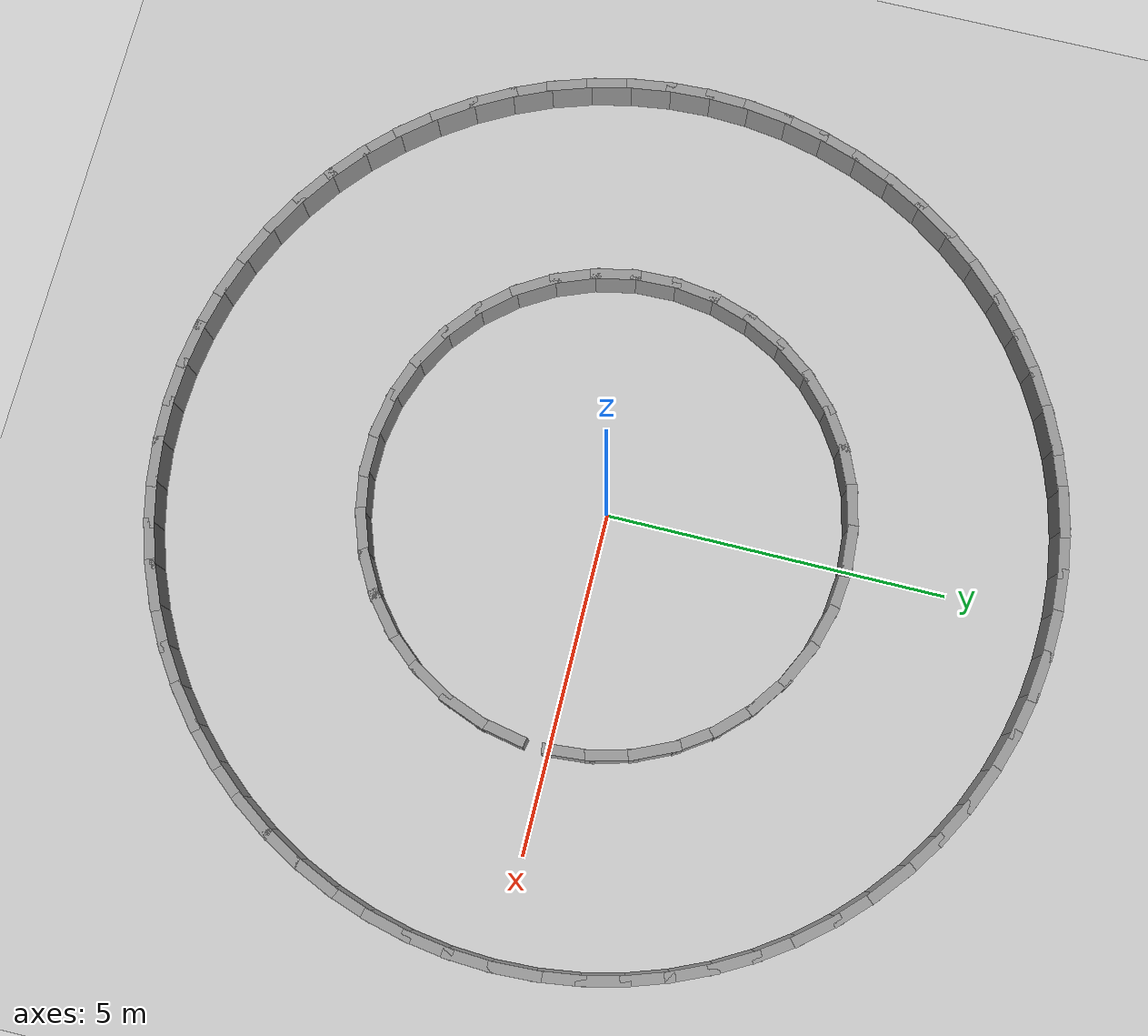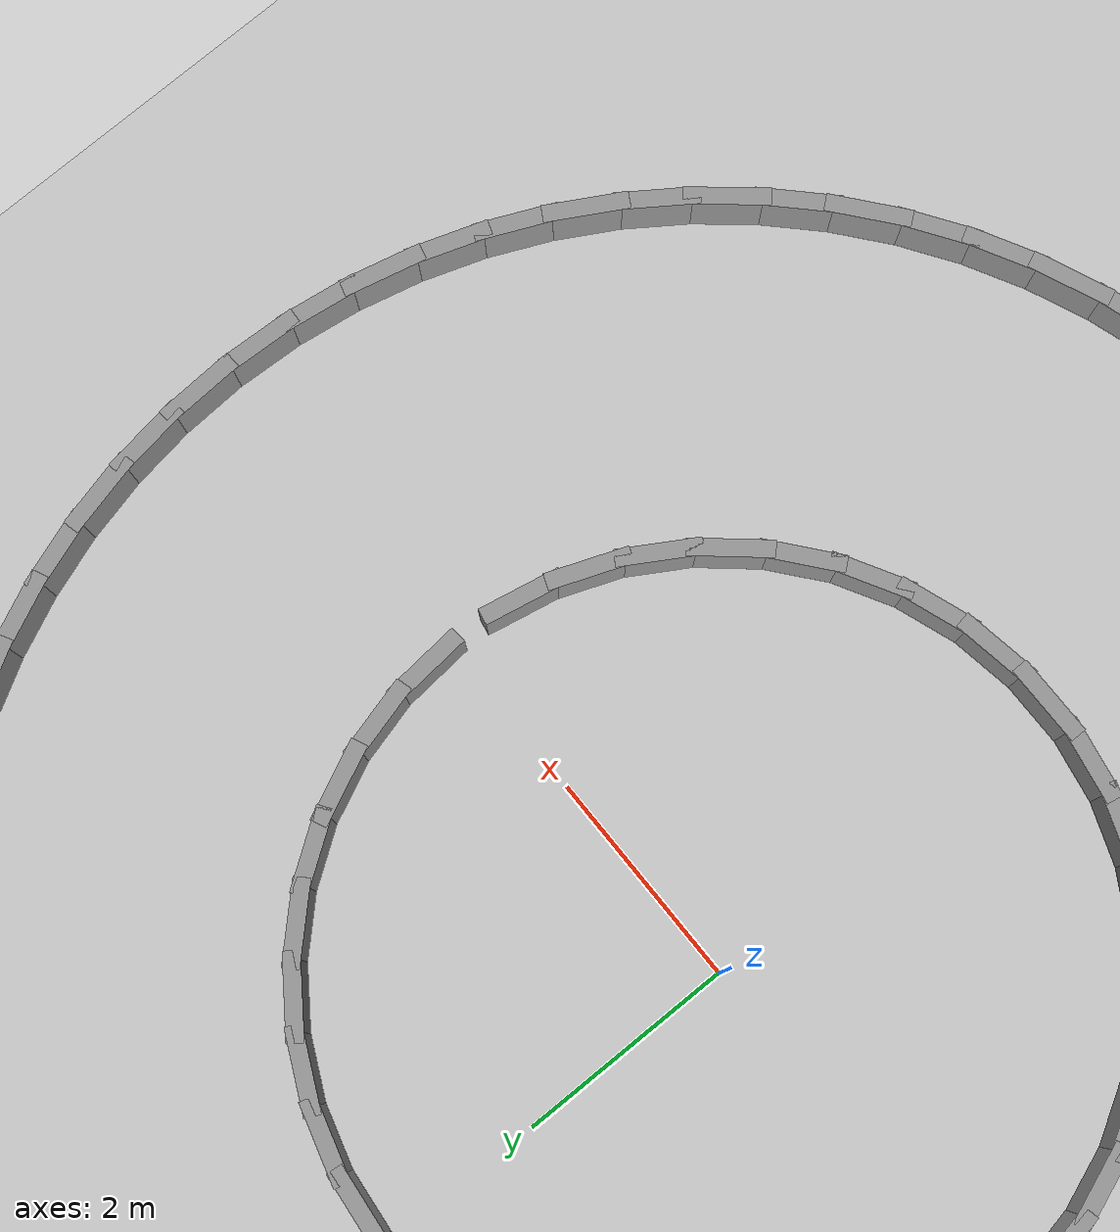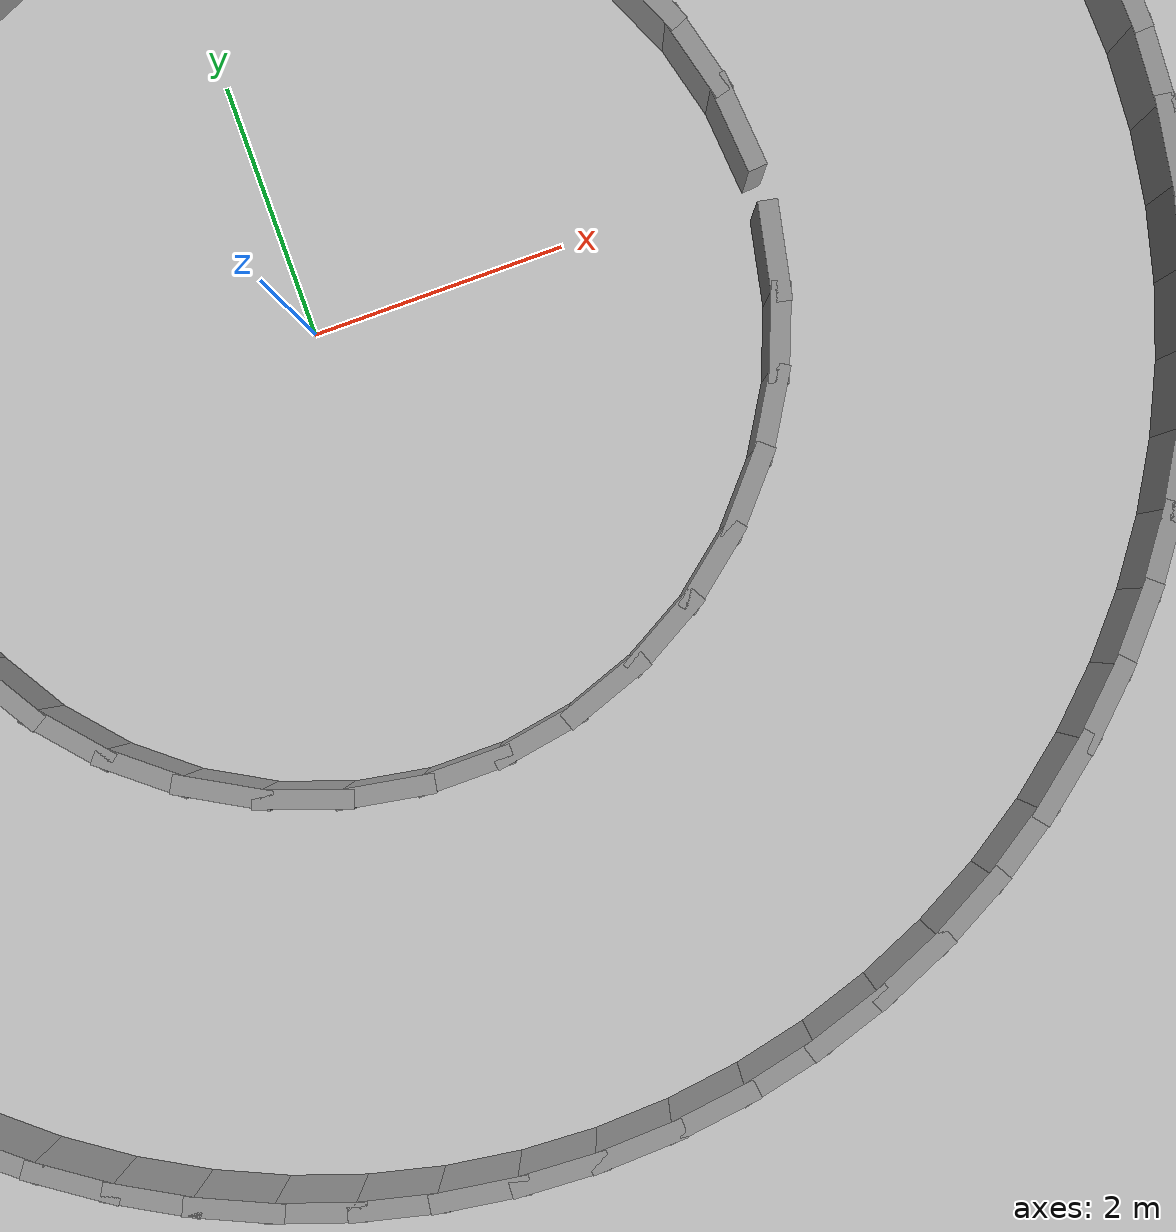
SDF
<?xml version="1.0" ?>
<sdf version='1.7'>
  <world name='default'>
    <plugin name='gazebo_ros_state' filename='libgazebo_ros_state.so'>
      <ros>
        <namespace>/</namespace>
      </ros>
      <update_rate>1000.0</update_rate>
    </plugin>

    <light name='sun' type='directional'>
      <cast_shadows>1</cast_shadows>
      <pose>0 0 10 0 -0 0</pose>
      <diffuse>0.8 0.8 0.8 1</diffuse>
      <specular>0.2 0.2 0.2 1</specular>
      <attenuation>
        <range>1000</range>
        <constant>0.9</constant>
        <linear>0.01</linear>
        <quadratic>0.001</quadratic>
      </attenuation>
      <direction>-0.5 0.1 -0.9</direction>
      <spot>
        <inner_angle>0</inner_angle>
        <outer_angle>0</outer_angle>
        <falloff>0</falloff>
      </spot>
    </light>
    <model name='ground_plane'>
      <static>1</static>
      <link name='link'>
        <collision name='collision'>
          <geometry>
            <plane>
              <normal>0 0 1</normal>
              <size>100 100</size>
            </plane>
          </geometry>
          <surface>
            <friction>
              <ode>
                <mu>100</mu>
                <mu2>50</mu2>
              </ode>
              <torsional>
                <ode/>
              </torsional>
            </friction>
            <contact>
              <ode/>
            </contact>
            <bounce/>
          </surface>
          <max_contacts>10</max_contacts>
        </collision>
        <visual name='visual'>
          <cast_shadows>0</cast_shadows>
          <geometry>
            <plane>
              <normal>0 0 1</normal>
              <size>100 100</size>
            </plane>
          </geometry>
          <material>
            <script>
              <uri>file://media/materials/scripts/gazebo.material</uri>
              <name>Gazebo/Grey</name>
            </script>
          </material>
        </visual>
        <self_collide>0</self_collide>
        <enable_wind>0</enable_wind>
        <kinematic>0</kinematic>
      </link>
    </model>
    <gravity>0 0 -9.8</gravity>
    <magnetic_field>6e-06 2.3e-05 -4.2e-05</magnetic_field>
    <atmosphere type='adiabatic'/>
    <physics type='ode'>
      <max_step_size>0.001</max_step_size>
      <real_time_factor>1</real_time_factor>
      <real_time_update_rate>1000</real_time_update_rate>
    </physics>
    <scene>
      <ambient>0.4 0.4 0.4 1</ambient>
      <background>0.7 0.7 0.7 1</background>
      <shadows>1</shadows>
    </scene>
    <audio>
      <device>default</device>
    </audio>
    <wind/>
    <spherical_coordinates>
      <surface_model>EARTH_WGS84</surface_model>
      <latitude_deg>0</latitude_deg>
      <longitude_deg>0</longitude_deg>
      <elevation>0</elevation>
      <heading_deg>0</heading_deg>
    </spherical_coordinates>
  <model name='roundabout_small'>
    <pose>0 0 0 0 -0 0</pose>
    <link name='Wall_0'>
      <collision name='Wall_0_Collision'>
        <geometry><box><size>0.7493 0.1500 0.6000</size></box></geometry>
        <pose>0 0 0.3000 0 -0 0</pose>
      </collision>
      <visual name='Wall_0_Visual'>
        <pose>0 0 0.3000 0 -0 0</pose>
        <geometry><box><size>0.7493 0.1500 0.6000</size></box></geometry>
        <material>
          <script>
            <uri>file://media/materials/scripts/gazebo.material</uri>
            <name>Gazebo/Grey</name>
          </script>
          <ambient>1 1 1 1</ambient>
        </material>
      </visual>
      <pose>3.4743 0.2985 0 0 -0 1.65653</pose>
    </link>
    <link name='Wall_1'>
      <collision name='Wall_1_Collision'>
        <geometry><box><size>0.7493 0.1500 0.6000</size></box></geometry>
        <pose>0 0 0.3000 0 -0 0</pose>
      </collision>
      <visual name='Wall_1_Visual'>
        <pose>0 0 0.3000 0 -0 0</pose>
        <geometry><box><size>0.7493 0.1500 0.6000</size></box></geometry>
        <material>
          <script>
            <uri>file://media/materials/scripts/gazebo.material</uri>
            <name>Gazebo/Grey</name>
          </script>
          <ambient>1 1 1 1</ambient>
        </material>
      </visual>
      <pose>3.3725 0.8868 0 0 -0 1.82794</pose>
    </link>
    <link name='Wall_2'>
      <collision name='Wall_2_Collision'>
        <geometry><box><size>0.7493 0.1500 0.6000</size></box></geometry>
        <pose>0 0 0.3000 0 -0 0</pose>
      </collision>
      <visual name='Wall_2_Visual'>
        <pose>0 0 0.3000 0 -0 0</pose>
        <geometry><box><size>0.7493 0.1500 0.6000</size></box></geometry>
        <material>
          <script>
            <uri>file://media/materials/scripts/gazebo.material</uri>
            <name>Gazebo/Grey</name>
          </script>
          <ambient>1 1 1 1</ambient>
        </material>
      </visual>
      <pose>3.1718 1.4492 0 0 -0 1.99935</pose>
    </link>
    <link name='Wall_3'>
      <collision name='Wall_3_Collision'>
        <geometry><box><size>0.7493 0.1500 0.6000</size></box></geometry>
        <pose>0 0 0.3000 0 -0 0</pose>
      </collision>
      <visual name='Wall_3_Visual'>
        <pose>0 0 0.3000 0 -0 0</pose>
        <geometry><box><size>0.7493 0.1500 0.6000</size></box></geometry>
        <material>
          <script>
            <uri>file://media/materials/scripts/gazebo.material</uri>
            <name>Gazebo/Grey</name>
          </script>
          <ambient>1 1 1 1</ambient>
        </material>
      </visual>
      <pose>2.8781 1.9690 0 0 -0 2.17080</pose>
    </link>
    <link name='Wall_4'>
      <collision name='Wall_4_Collision'>
        <geometry><box><size>0.7493 0.1500 0.6000</size></box></geometry>
        <pose>0 0 0.3000 0 -0 0</pose>
      </collision>
      <visual name='Wall_4_Visual'>
        <pose>0 0 0.3000 0 -0 0</pose>
        <geometry><box><size>0.7493 0.1500 0.6000</size></box></geometry>
        <material>
          <script>
            <uri>file://media/materials/scripts/gazebo.material</uri>
            <name>Gazebo/Grey</name>
          </script>
          <ambient>1 1 1 1</ambient>
        </material>
      </visual>
      <pose>2.5000 2.4311 0 0 -0 2.34224</pose>
    </link>
    <link name='Wall_5'>
      <collision name='Wall_5_Collision'>
        <geometry><box><size>0.7493 0.1500 0.6000</size></box></geometry>
        <pose>0 0 0.3000 0 -0 0</pose>
      </collision>
      <visual name='Wall_5_Visual'>
        <pose>0 0 0.3000 0 -0 0</pose>
        <geometry><box><size>0.7493 0.1500 0.6000</size></box></geometry>
        <material>
          <script>
            <uri>file://media/materials/scripts/gazebo.material</uri>
            <name>Gazebo/Grey</name>
          </script>
          <ambient>1 1 1 1</ambient>
        </material>
      </visual>
      <pose>2.0486 2.8219 0 0 -0 2.51365</pose>
    </link>
    <link name='Wall_6'>
      <collision name='Wall_6_Collision'>
        <geometry><box><size>0.7493 0.1500 0.6000</size></box></geometry>
        <pose>0 0 0.3000 0 -0 0</pose>
      </collision>
      <visual name='Wall_6_Visual'>
        <pose>0 0 0.3000 0 -0 0</pose>
        <geometry><box><size>0.7493 0.1500 0.6000</size></box></geometry>
        <material>
          <script>
            <uri>file://media/materials/scripts/gazebo.material</uri>
            <name>Gazebo/Grey</name>
          </script>
          <ambient>1 1 1 1</ambient>
        </material>
      </visual>
      <pose>1.5372 3.1300 0 0 -0 2.68506</pose>
    </link>
    <link name='Wall_7'>
      <collision name='Wall_7_Collision'>
        <geometry><box><size>0.7493 0.1500 0.6000</size></box></geometry>
        <pose>0 0 0.3000 0 -0 0</pose>
      </collision>
      <visual name='Wall_7_Visual'>
        <pose>0 0 0.3000 0 -0 0</pose>
        <geometry><box><size>0.7493 0.1500 0.6000</size></box></geometry>
        <material>
          <script>
            <uri>file://media/materials/scripts/gazebo.material</uri>
            <name>Gazebo/Grey</name>
          </script>
          <ambient>1 1 1 1</ambient>
        </material>
      </visual>
      <pose>0.9807 3.3464 0 0 -0 2.85653</pose>
    </link>
    <link name='Wall_8'>
      <collision name='Wall_8_Collision'>
        <geometry><box><size>0.7493 0.1500 0.6000</size></box></geometry>
        <pose>0 0 0.3000 0 -0 0</pose>
      </collision>
      <visual name='Wall_8_Visual'>
        <pose>0 0 0.3000 0 -0 0</pose>
        <geometry><box><size>0.7493 0.1500 0.6000</size></box></geometry>
        <material>
          <script>
            <uri>file://media/materials/scripts/gazebo.material</uri>
            <name>Gazebo/Grey</name>
          </script>
          <ambient>1 1 1 1</ambient>
        </material>
      </visual>
      <pose>0.3955 3.4646 0 0 -0 3.02795</pose>
    </link>
    <link name='Wall_9'>
      <collision name='Wall_9_Collision'>
        <geometry><box><size>0.7493 0.1500 0.6000</size></box></geometry>
        <pose>0 0 0.3000 0 -0 0</pose>
      </collision>
      <visual name='Wall_9_Visual'>
        <pose>0 0 0.3000 0 -0 0</pose>
        <geometry><box><size>0.7493 0.1500 0.6000</size></box></geometry>
        <material>
          <script>
            <uri>file://media/materials/scripts/gazebo.material</uri>
            <name>Gazebo/Grey</name>
          </script>
          <ambient>1 1 1 1</ambient>
        </material>
      </visual>
      <pose>-0.2014 3.4813 0 0 -0 -3.08383</pose>
    </link>
    <link name='Wall_10'>
      <collision name='Wall_10_Collision'>
        <geometry><box><size>0.7493 0.1500 0.6000</size></box></geometry>
        <pose>0 0 0.3000 0 -0 0</pose>
      </collision>
      <visual name='Wall_10_Visual'>
        <pose>0 0 0.3000 0 -0 0</pose>
        <geometry><box><size>0.7493 0.1500 0.6000</size></box></geometry>
        <material>
          <script>
            <uri>file://media/materials/scripts/gazebo.material</uri>
            <name>Gazebo/Grey</name>
          </script>
          <ambient>1 1 1 1</ambient>
        </material>
      </visual>
      <pose>-0.7923 3.3959 0 0 -0 -2.91239</pose>
    </link>
    <link name='Wall_11'>
      <collision name='Wall_11_Collision'>
        <geometry><box><size>0.7493 0.1500 0.6000</size></box></geometry>
        <pose>0 0 0.3000 0 -0 0</pose>
      </collision>
      <visual name='Wall_11_Visual'>
        <pose>0 0 0.3000 0 -0 0</pose>
        <geometry><box><size>0.7493 0.1500 0.6000</size></box></geometry>
        <material>
          <script>
            <uri>file://media/materials/scripts/gazebo.material</uri>
            <name>Gazebo/Grey</name>
          </script>
          <ambient>1 1 1 1</ambient>
        </material>
      </visual>
      <pose>-1.3600 3.2110 0 0 -0 -2.74094</pose>
    </link>
    <link name='Wall_12'>
      <collision name='Wall_12_Collision'>
        <geometry><box><size>0.7493 0.1500 0.6000</size></box></geometry>
        <pose>0 0 0.3000 0 -0 0</pose>
      </collision>
      <visual name='Wall_12_Visual'>
        <pose>0 0 0.3000 0 -0 0</pose>
        <geometry><box><size>0.7493 0.1500 0.6000</size></box></geometry>
        <material>
          <script>
            <uri>file://media/materials/scripts/gazebo.material</uri>
            <name>Gazebo/Grey</name>
          </script>
          <ambient>1 1 1 1</ambient>
        </material>
      </visual>
      <pose>-1.8878 2.9319 0 0 -0 -2.56953</pose>
    </link>
    <link name='Wall_13'>
      <collision name='Wall_13_Collision'>
        <geometry><box><size>0.7493 0.1500 0.6000</size></box></geometry>
        <pose>0 0 0.3000 0 -0 0</pose>
      </collision>
      <visual name='Wall_13_Visual'>
        <pose>0 0 0.3000 0 -0 0</pose>
        <geometry><box><size>0.7493 0.1500 0.6000</size></box></geometry>
        <material>
          <script>
            <uri>file://media/materials/scripts/gazebo.material</uri>
            <name>Gazebo/Grey</name>
          </script>
          <ambient>1 1 1 1</ambient>
        </material>
      </visual>
      <pose>-2.3603 2.5669 0 0 -0 -2.39812</pose>
    </link>
    <link name='Wall_14'>
      <collision name='Wall_14_Collision'>
        <geometry><box><size>0.7493 0.1500 0.6000</size></box></geometry>
        <pose>0 0 0.3000 0 -0 0</pose>
      </collision>
      <visual name='Wall_14_Visual'>
        <pose>0 0 0.3000 0 -0 0</pose>
        <geometry><box><size>0.7493 0.1500 0.6000</size></box></geometry>
        <material>
          <script>
            <uri>file://media/materials/scripts/gazebo.material</uri>
            <name>Gazebo/Grey</name>
          </script>
          <ambient>1 1 1 1</ambient>
        </material>
      </visual>
      <pose>-2.7636 2.1266 0 0 -0 -2.22665</pose>
    </link>
    <link name='Wall_15'>
      <collision name='Wall_15_Collision'>
        <geometry><box><size>0.7493 0.1500 0.6000</size></box></geometry>
        <pose>0 0 0.3000 0 -0 0</pose>
      </collision>
      <visual name='Wall_15_Visual'>
        <pose>0 0 0.3000 0 -0 0</pose>
        <geometry><box><size>0.7493 0.1500 0.6000</size></box></geometry>
        <material>
          <script>
            <uri>file://media/materials/scripts/gazebo.material</uri>
            <name>Gazebo/Grey</name>
          </script>
          <ambient>1 1 1 1</ambient>
        </material>
      </visual>
      <pose>-3.0859 1.6240 0 0 -0 -2.05524</pose>
    </link>
    <link name='Wall_16'>
      <collision name='Wall_16_Collision'>
        <geometry><box><size>0.7493 0.1500 0.6000</size></box></geometry>
        <pose>0 0 0.3000 0 -0 0</pose>
      </collision>
      <visual name='Wall_16_Visual'>
        <pose>0 0 0.3000 0 -0 0</pose>
        <geometry><box><size>0.7493 0.1500 0.6000</size></box></geometry>
        <material>
          <script>
            <uri>file://media/materials/scripts/gazebo.material</uri>
            <name>Gazebo/Grey</name>
          </script>
          <ambient>1 1 1 1</ambient>
        </material>
      </visual>
      <pose>-3.3177 1.0738 0 0 -0 -1.88382</pose>
    </link>
    <link name='Wall_17'>
      <collision name='Wall_17_Collision'>
        <geometry><box><size>0.7493 0.1500 0.6000</size></box></geometry>
        <pose>0 0 0.3000 0 -0 0</pose>
      </collision>
      <visual name='Wall_17_Visual'>
        <pose>0 0 0.3000 0 -0 0</pose>
        <geometry><box><size>0.7493 0.1500 0.6000</size></box></geometry>
        <material>
          <script>
            <uri>file://media/materials/scripts/gazebo.material</uri>
            <name>Gazebo/Grey</name>
          </script>
          <ambient>1 1 1 1</ambient>
        </material>
      </visual>
      <pose>-3.4522 0.4921 0 0 -0 -1.71239</pose>
    </link>
    <link name='Wall_18'>
      <collision name='Wall_18_Collision'>
        <geometry><box><size>0.7493 0.1500 0.6000</size></box></geometry>
        <pose>0 0 0.3000 0 -0 0</pose>
      </collision>
      <visual name='Wall_18_Visual'>
        <pose>0 0 0.3000 0 -0 0</pose>
        <geometry><box><size>0.7493 0.1500 0.6000</size></box></geometry>
        <material>
          <script>
            <uri>file://media/materials/scripts/gazebo.material</uri>
            <name>Gazebo/Grey</name>
          </script>
          <ambient>1 1 1 1</ambient>
        </material>
      </visual>
      <pose>-3.4856 -0.1040 0 0 -0 -1.54094</pose>
    </link>
    <link name='Wall_19'>
      <collision name='Wall_19_Collision'>
        <geometry><box><size>0.7493 0.1500 0.6000</size></box></geometry>
        <pose>0 0 0.3000 0 -0 0</pose>
      </collision>
      <visual name='Wall_19_Visual'>
        <pose>0 0 0.3000 0 -0 0</pose>
        <geometry><box><size>0.7493 0.1500 0.6000</size></box></geometry>
        <material>
          <script>
            <uri>file://media/materials/scripts/gazebo.material</uri>
            <name>Gazebo/Grey</name>
          </script>
          <ambient>1 1 1 1</ambient>
        </material>
      </visual>
      <pose>-3.4167 -0.6971 0 0 -0 -1.36953</pose>
    </link>
    <link name='Wall_20'>
      <collision name='Wall_20_Collision'>
        <geometry><box><size>0.7493 0.1500 0.6000</size></box></geometry>
        <pose>0 0 0.3000 0 -0 0</pose>
      </collision>
      <visual name='Wall_20_Visual'>
        <pose>0 0 0.3000 0 -0 0</pose>
        <geometry><box><size>0.7493 0.1500 0.6000</size></box></geometry>
        <material>
          <script>
            <uri>file://media/materials/scripts/gazebo.material</uri>
            <name>Gazebo/Grey</name>
          </script>
          <ambient>1 1 1 1</ambient>
        </material>
      </visual>
      <pose>-3.2477 -1.2698 0 0 -0 -1.19812</pose>
    </link>
    <link name='Wall_21'>
      <collision name='Wall_21_Collision'>
        <geometry><box><size>0.7493 0.1500 0.6000</size></box></geometry>
        <pose>0 0 0.3000 0 -0 0</pose>
      </collision>
      <visual name='Wall_21_Visual'>
        <pose>0 0 0.3000 0 -0 0</pose>
        <geometry><box><size>0.7493 0.1500 0.6000</size></box></geometry>
        <material>
          <script>
            <uri>file://media/materials/scripts/gazebo.material</uri>
            <name>Gazebo/Grey</name>
          </script>
          <ambient>1 1 1 1</ambient>
        </material>
      </visual>
      <pose>-2.9835 -1.8052 0 0 -0 -1.02665</pose>
    </link>
    <link name='Wall_22'>
      <collision name='Wall_22_Collision'>
        <geometry><box><size>0.7493 0.1500 0.6000</size></box></geometry>
        <pose>0 0 0.3000 0 -0 0</pose>
      </collision>
      <visual name='Wall_22_Visual'>
        <pose>0 0 0.3000 0 -0 0</pose>
        <geometry><box><size>0.7493 0.1500 0.6000</size></box></geometry>
        <material>
          <script>
            <uri>file://media/materials/scripts/gazebo.material</uri>
            <name>Gazebo/Grey</name>
          </script>
          <ambient>1 1 1 1</ambient>
        </material>
      </visual>
      <pose>-2.6318 -2.2877 0 0 -0 -0.85523</pose>
    </link>
    <link name='Wall_23'>
      <collision name='Wall_23_Collision'>
        <geometry><box><size>0.7493 0.1500 0.6000</size></box></geometry>
        <pose>0 0 0.3000 0 -0 0</pose>
      </collision>
      <visual name='Wall_23_Visual'>
        <pose>0 0 0.3000 0 -0 0</pose>
        <geometry><box><size>0.7493 0.1500 0.6000</size></box></geometry>
        <material>
          <script>
            <uri>file://media/materials/scripts/gazebo.material</uri>
            <name>Gazebo/Grey</name>
          </script>
          <ambient>1 1 1 1</ambient>
        </material>
      </visual>
      <pose>-2.2030 -2.7031 0 0 -0 -0.68382</pose>
    </link>
    <link name='Wall_24'>
      <collision name='Wall_24_Collision'>
        <geometry><box><size>0.7493 0.1500 0.6000</size></box></geometry>
        <pose>0 0 0.3000 0 -0 0</pose>
      </collision>
      <visual name='Wall_24_Visual'>
        <pose>0 0 0.3000 0 -0 0</pose>
        <geometry><box><size>0.7493 0.1500 0.6000</size></box></geometry>
        <material>
          <script>
            <uri>file://media/materials/scripts/gazebo.material</uri>
            <name>Gazebo/Grey</name>
          </script>
          <ambient>1 1 1 1</ambient>
        </material>
      </visual>
      <pose>-1.7096 -3.0393 0 0 -0 -0.51239</pose>
    </link>
    <link name='Wall_25'>
      <collision name='Wall_25_Collision'>
        <geometry><box><size>0.7493 0.1500 0.6000</size></box></geometry>
        <pose>0 0 0.3000 0 -0 0</pose>
      </collision>
      <visual name='Wall_25_Visual'>
        <pose>0 0 0.3000 0 -0 0</pose>
        <geometry><box><size>0.7493 0.1500 0.6000</size></box></geometry>
        <material>
          <script>
            <uri>file://media/materials/scripts/gazebo.material</uri>
            <name>Gazebo/Grey</name>
          </script>
          <ambient>1 1 1 1</ambient>
        </material>
      </visual>
      <pose>-1.1660 -3.2864 0 0 -0 -0.34094</pose>
    </link>
    <link name='Wall_26'>
      <collision name='Wall_26_Collision'>
        <geometry><box><size>0.7493 0.1500 0.6000</size></box></geometry>
        <pose>0 0 0.3000 0 -0 0</pose>
      </collision>
      <visual name='Wall_26_Visual'>
        <pose>0 0 0.3000 0 -0 0</pose>
        <geometry><box><size>0.7493 0.1500 0.6000</size></box></geometry>
        <material>
          <script>
            <uri>file://media/materials/scripts/gazebo.material</uri>
            <name>Gazebo/Grey</name>
          </script>
          <ambient>1 1 1 1</ambient>
        </material>
      </visual>
      <pose>-0.5883 -3.4371 0 0 -0 -0.16953</pose>
    </link>
    <link name='Wall_27'>
      <collision name='Wall_27_Collision'>
        <geometry><box><size>0.7493 0.1500 0.6000</size></box></geometry>
        <pose>0 0 0.3000 0 -0 0</pose>
      </collision>
      <visual name='Wall_27_Visual'>
        <pose>0 0 0.3000 0 -0 0</pose>
        <geometry><box><size>0.7493 0.1500 0.6000</size></box></geometry>
        <material>
          <script>
            <uri>file://media/materials/scripts/gazebo.material</uri>
            <name>Gazebo/Grey</name>
          </script>
          <ambient>1 1 1 1</ambient>
        </material>
      </visual>
      <pose>0.0066 -3.4871 0 0 -0 0.00188</pose>
    </link>
    <link name='Wall_28'>
      <collision name='Wall_28_Collision'>
        <geometry><box><size>0.7493 0.1500 0.6000</size></box></geometry>
        <pose>0 0 0.3000 0 -0 0</pose>
      </collision>
      <visual name='Wall_28_Visual'>
        <pose>0 0 0.3000 0 -0 0</pose>
        <geometry><box><size>0.7493 0.1500 0.6000</size></box></geometry>
        <material>
          <script>
            <uri>file://media/materials/scripts/gazebo.material</uri>
            <name>Gazebo/Grey</name>
          </script>
          <ambient>1 1 1 1</ambient>
        </material>
      </visual>
      <pose>0.6014 -3.4349 0 0 -0 0.17335</pose>
    </link>
    <link name='Wall_29'>
      <collision name='Wall_29_Collision'>
        <geometry><box><size>0.7493 0.1500 0.6000</size></box></geometry>
        <pose>0 0 0.3000 0 -0 0</pose>
      </collision>
      <visual name='Wall_29_Visual'>
        <pose>0 0 0.3000 0 -0 0</pose>
        <geometry><box><size>0.7493 0.1500 0.6000</size></box></geometry>
        <material>
          <script>
            <uri>file://media/materials/scripts/gazebo.material</uri>
            <name>Gazebo/Grey</name>
          </script>
          <ambient>1 1 1 1</ambient>
        </material>
      </visual>
      <pose>1.1786 -3.2819 0 0 -0 0.34477</pose>
    </link>
    <link name='Wall_30'>
      <collision name='Wall_30_Collision'>
        <geometry><box><size>0.7493 0.1500 0.6000</size></box></geometry>
        <pose>0 0 0.3000 0 -0 0</pose>
      </collision>
      <visual name='Wall_30_Visual'>
        <pose>0 0 0.3000 0 -0 0</pose>
        <geometry><box><size>0.7493 0.1500 0.6000</size></box></geometry>
        <material>
          <script>
            <uri>file://media/materials/scripts/gazebo.material</uri>
            <name>Gazebo/Grey</name>
          </script>
          <ambient>1 1 1 1</ambient>
        </material>
      </visual>
      <pose>1.7211 -3.0328 0 0 -0 0.51618</pose>
    </link>
    <link name='Wall_31'>
      <collision name='Wall_31_Collision'>
        <geometry><box><size>0.7493 0.1500 0.6000</size></box></geometry>
        <pose>0 0 0.3000 0 -0 0</pose>
      </collision>
      <visual name='Wall_31_Visual'>
        <pose>0 0 0.3000 0 -0 0</pose>
        <geometry><box><size>0.7493 0.1500 0.6000</size></box></geometry>
        <material>
          <script>
            <uri>file://media/materials/scripts/gazebo.material</uri>
            <name>Gazebo/Grey</name>
          </script>
          <ambient>1 1 1 1</ambient>
        </material>
      </visual>
      <pose>2.2133 -2.6947 0 0 -0 0.68761</pose>
    </link>
    <link name='Wall_32'>
      <collision name='Wall_32_Collision'>
        <geometry><box><size>0.7493 0.1500 0.6000</size></box></geometry>
        <pose>0 0 0.3000 0 -0 0</pose>
      </collision>
      <visual name='Wall_32_Visual'>
        <pose>0 0 0.3000 0 -0 0</pose>
        <geometry><box><size>0.7493 0.1500 0.6000</size></box></geometry>
        <material>
          <script>
            <uri>file://media/materials/scripts/gazebo.material</uri>
            <name>Gazebo/Grey</name>
          </script>
          <ambient>1 1 1 1</ambient>
        </material>
      </visual>
      <pose>2.6405 -2.2777 0 0 -0 0.85907</pose>
    </link>
    <link name='Wall_33'>
      <collision name='Wall_33_Collision'>
        <geometry><box><size>0.7493 0.1500 0.6000</size></box></geometry>
        <pose>0 0 0.3000 0 -0 0</pose>
      </collision>
      <visual name='Wall_33_Visual'>
        <pose>0 0 0.3000 0 -0 0</pose>
        <geometry><box><size>0.7493 0.1500 0.6000</size></box></geometry>
        <material>
          <script>
            <uri>file://media/materials/scripts/gazebo.material</uri>
            <name>Gazebo/Grey</name>
          </script>
          <ambient>1 1 1 1</ambient>
        </material>
      </visual>
      <pose>2.9904 -1.7938 0 0 -0 1.03048</pose>
    </link>
    <link name='Wall_34'>
      <collision name='Wall_34_Collision'>
        <geometry><box><size>0.7493 0.1500 0.6000</size></box></geometry>
        <pose>0 0 0.3000 0 -0 0</pose>
      </collision>
      <visual name='Wall_34_Visual'>
        <pose>0 0 0.3000 0 -0 0</pose>
        <geometry><box><size>0.7493 0.1500 0.6000</size></box></geometry>
        <material>
          <script>
            <uri>file://media/materials/scripts/gazebo.material</uri>
            <name>Gazebo/Grey</name>
          </script>
          <ambient>1 1 1 1</ambient>
        </material>
      </visual>
      <pose>3.2526 -1.2574 0 0 -0 1.20189</pose>
    </link>
    <link name='Wall_35'>
      <collision name='Wall_35_Collision'>
        <geometry><box><size>0.7493 0.1500 0.6000</size></box></geometry>
        <pose>0 0 0.3000 0 -0 0</pose>
      </collision>
      <visual name='Wall_35_Visual'>
        <pose>0 0 0.3000 0 -0 0</pose>
        <geometry><box><size>0.7493 0.1500 0.6000</size></box></geometry>
        <material>
          <script>
            <uri>file://media/materials/scripts/gazebo.material</uri>
            <name>Gazebo/Grey</name>
          </script>
          <ambient>1 1 1 1</ambient>
        </material>
      </visual>
      <pose>3.4194 -0.6841 0 0 -0 1.37335</pose>
    </link>
    <link name='Wall_36'>
      <collision name='Wall_36_Collision'>
        <geometry><box><size>0.7498 0.1500 0.6000</size></box></geometry>
        <pose>0 0 0.3000 0 -0 0</pose>
      </collision>
      <visual name='Wall_36_Visual'>
        <pose>0 0 0.3000 0 -0 0</pose>
        <geometry><box><size>0.7498 0.1500 0.6000</size></box></geometry>
        <material>
          <script>
            <uri>file://media/materials/scripts/gazebo.material</uri>
            <name>Gazebo/Grey</name>
          </script>
          <ambient>1 1 1 1</ambient>
        </material>
      </visual>
      <pose>6.4861 0.2996 0 0 -0 1.61700</pose>
    </link>
    <link name='Wall_37'>
      <collision name='Wall_37_Collision'>
        <geometry><box><size>0.7498 0.1500 0.6000</size></box></geometry>
        <pose>0 0 0.3000 0 -0 0</pose>
      </collision>
      <visual name='Wall_37_Visual'>
        <pose>0 0 0.3000 0 -0 0</pose>
        <geometry><box><size>0.7498 0.1500 0.6000</size></box></geometry>
        <material>
          <script>
            <uri>file://media/materials/scripts/gazebo.material</uri>
            <name>Gazebo/Grey</name>
          </script>
          <ambient>1 1 1 1</ambient>
        </material>
      </visual>
      <pose>6.4309 0.8962 0 0 -0 1.70926</pose>
    </link>
    <link name='Wall_38'>
      <collision name='Wall_38_Collision'>
        <geometry><box><size>0.7498 0.1500 0.6000</size></box></geometry>
        <pose>0 0 0.3000 0 -0 0</pose>
      </collision>
      <visual name='Wall_38_Visual'>
        <pose>0 0 0.3000 0 -0 0</pose>
        <geometry><box><size>0.7498 0.1500 0.6000</size></box></geometry>
        <material>
          <script>
            <uri>file://media/materials/scripts/gazebo.material</uri>
            <name>Gazebo/Grey</name>
          </script>
          <ambient>1 1 1 1</ambient>
        </material>
      </visual>
      <pose>6.3209 1.4851 0 0 -0 1.80153</pose>
    </link>
    <link name='Wall_39'>
      <collision name='Wall_39_Collision'>
        <geometry><box><size>0.7498 0.1500 0.6000</size></box></geometry>
        <pose>0 0 0.3000 0 -0 0</pose>
      </collision>
      <visual name='Wall_39_Visual'>
        <pose>0 0 0.3000 0 -0 0</pose>
        <geometry><box><size>0.7498 0.1500 0.6000</size></box></geometry>
        <material>
          <script>
            <uri>file://media/materials/scripts/gazebo.material</uri>
            <name>Gazebo/Grey</name>
          </script>
          <ambient>1 1 1 1</ambient>
        </material>
      </visual>
      <pose>6.1571 2.0615 0 0 -0 1.89390</pose>
    </link>
    <link name='Wall_40'>
      <collision name='Wall_40_Collision'>
        <geometry><box><size>0.7498 0.1500 0.6000</size></box></geometry>
        <pose>0 0 0.3000 0 -0 0</pose>
      </collision>
      <visual name='Wall_40_Visual'>
        <pose>0 0 0.3000 0 -0 0</pose>
        <geometry><box><size>0.7498 0.1500 0.6000</size></box></geometry>
        <material>
          <script>
            <uri>file://media/materials/scripts/gazebo.material</uri>
            <name>Gazebo/Grey</name>
          </script>
          <ambient>1 1 1 1</ambient>
        </material>
      </visual>
      <pose>5.9409 2.6202 0 0 -0 1.98620</pose>
    </link>
    <link name='Wall_41'>
      <collision name='Wall_41_Collision'>
        <geometry><box><size>0.7498 0.1500 0.6000</size></box></geometry>
        <pose>0 0 0.3000 0 -0 0</pose>
      </collision>
      <visual name='Wall_41_Visual'>
        <pose>0 0 0.3000 0 -0 0</pose>
        <geometry><box><size>0.7498 0.1500 0.6000</size></box></geometry>
        <material>
          <script>
            <uri>file://media/materials/scripts/gazebo.material</uri>
            <name>Gazebo/Grey</name>
          </script>
          <ambient>1 1 1 1</ambient>
        </material>
      </visual>
      <pose>5.6741 3.1567 0 0 -0 2.07846</pose>
    </link>
    <link name='Wall_42'>
      <collision name='Wall_42_Collision'>
        <geometry><box><size>0.7498 0.1500 0.6000</size></box></geometry>
        <pose>0 0 0.3000 0 -0 0</pose>
      </collision>
      <visual name='Wall_42_Visual'>
        <pose>0 0 0.3000 0 -0 0</pose>
        <geometry><box><size>0.7498 0.1500 0.6000</size></box></geometry>
        <material>
          <script>
            <uri>file://media/materials/scripts/gazebo.material</uri>
            <name>Gazebo/Grey</name>
          </script>
          <ambient>1 1 1 1</ambient>
        </material>
      </visual>
      <pose>5.3590 3.6663 0 0 -0 2.17080</pose>
    </link>
    <link name='Wall_43'>
      <collision name='Wall_43_Collision'>
        <geometry><box><size>0.7498 0.1500 0.6000</size></box></geometry>
        <pose>0 0 0.3000 0 -0 0</pose>
      </collision>
      <visual name='Wall_43_Visual'>
        <pose>0 0 0.3000 0 -0 0</pose>
        <geometry><box><size>0.7498 0.1500 0.6000</size></box></geometry>
        <material>
          <script>
            <uri>file://media/materials/scripts/gazebo.material</uri>
            <name>Gazebo/Grey</name>
          </script>
          <ambient>1 1 1 1</ambient>
        </material>
      </visual>
      <pose>4.9982 4.1446 0 0 -0 2.26313</pose>
    </link>
    <link name='Wall_44'>
      <collision name='Wall_44_Collision'>
        <geometry><box><size>0.7498 0.1500 0.6000</size></box></geometry>
        <pose>0 0 0.3000 0 -0 0</pose>
      </collision>
      <visual name='Wall_44_Visual'>
        <pose>0 0 0.3000 0 -0 0</pose>
        <geometry><box><size>0.7498 0.1500 0.6000</size></box></geometry>
        <material>
          <script>
            <uri>file://media/materials/scripts/gazebo.material</uri>
            <name>Gazebo/Grey</name>
          </script>
          <ambient>1 1 1 1</ambient>
        </material>
      </visual>
      <pose>4.5949 4.5877 0 0 -0 2.35540</pose>
    </link>
    <link name='Wall_45'>
      <collision name='Wall_45_Collision'>
        <geometry><box><size>0.7498 0.1500 0.6000</size></box></geometry>
        <pose>0 0 0.3000 0 -0 0</pose>
      </collision>
      <visual name='Wall_45_Visual'>
        <pose>0 0 0.3000 0 -0 0</pose>
        <geometry><box><size>0.7498 0.1500 0.6000</size></box></geometry>
        <material>
          <script>
            <uri>file://media/materials/scripts/gazebo.material</uri>
            <name>Gazebo/Grey</name>
          </script>
          <ambient>1 1 1 1</ambient>
        </material>
      </visual>
      <pose>4.1524 4.9917 0 0 -0 2.44770</pose>
    </link>
    <link name='Wall_46'>
      <collision name='Wall_46_Collision'>
        <geometry><box><size>0.7498 0.1500 0.6000</size></box></geometry>
        <pose>0 0 0.3000 0 -0 0</pose>
      </collision>
      <visual name='Wall_46_Visual'>
        <pose>0 0 0.3000 0 -0 0</pose>
        <geometry><box><size>0.7498 0.1500 0.6000</size></box></geometry>
        <material>
          <script>
            <uri>file://media/materials/scripts/gazebo.material</uri>
            <name>Gazebo/Grey</name>
          </script>
          <ambient>1 1 1 1</ambient>
        </material>
      </visual>
      <pose>3.6746 5.3532 0 0 -0 2.54006</pose>
    </link>
    <link name='Wall_47'>
      <collision name='Wall_47_Collision'>
        <geometry><box><size>0.7498 0.1500 0.6000</size></box></geometry>
        <pose>0 0 0.3000 0 -0 0</pose>
      </collision>
      <visual name='Wall_47_Visual'>
        <pose>0 0 0.3000 0 -0 0</pose>
        <geometry><box><size>0.7498 0.1500 0.6000</size></box></geometry>
        <material>
          <script>
            <uri>file://media/materials/scripts/gazebo.material</uri>
            <name>Gazebo/Grey</name>
          </script>
          <ambient>1 1 1 1</ambient>
        </material>
      </visual>
      <pose>3.1655 5.6691 0 0 -0 2.63233</pose>
    </link>
    <link name='Wall_48'>
      <collision name='Wall_48_Collision'>
        <geometry><box><size>0.7498 0.1500 0.6000</size></box></geometry>
        <pose>0 0 0.3000 0 -0 0</pose>
      </collision>
      <visual name='Wall_48_Visual'>
        <pose>0 0 0.3000 0 -0 0</pose>
        <geometry><box><size>0.7498 0.1500 0.6000</size></box></geometry>
        <material>
          <script>
            <uri>file://media/materials/scripts/gazebo.material</uri>
            <name>Gazebo/Grey</name>
          </script>
          <ambient>1 1 1 1</ambient>
        </material>
      </visual>
      <pose>2.6295 5.9368 0 0 -0 2.72460</pose>
    </link>
    <link name='Wall_49'>
      <collision name='Wall_49_Collision'>
        <geometry><box><size>0.7498 0.1500 0.6000</size></box></geometry>
        <pose>0 0 0.3000 0 -0 0</pose>
      </collision>
      <visual name='Wall_49_Visual'>
        <pose>0 0 0.3000 0 -0 0</pose>
        <geometry><box><size>0.7498 0.1500 0.6000</size></box></geometry>
        <material>
          <script>
            <uri>file://media/materials/scripts/gazebo.material</uri>
            <name>Gazebo/Grey</name>
          </script>
          <ambient>1 1 1 1</ambient>
        </material>
      </visual>
      <pose>2.0711 6.1539 0 0 -0 2.81700</pose>
    </link>
    <link name='Wall_50'>
      <collision name='Wall_50_Collision'>
        <geometry><box><size>0.7498 0.1500 0.6000</size></box></geometry>
        <pose>0 0 0.3000 0 -0 0</pose>
      </collision>
      <visual name='Wall_50_Visual'>
        <pose>0 0 0.3000 0 -0 0</pose>
        <geometry><box><size>0.7498 0.1500 0.6000</size></box></geometry>
        <material>
          <script>
            <uri>file://media/materials/scripts/gazebo.material</uri>
            <name>Gazebo/Grey</name>
          </script>
          <ambient>1 1 1 1</ambient>
        </material>
      </visual>
      <pose>1.4950 6.3186 0 0 -0 2.90926</pose>
    </link>
    <link name='Wall_51'>
      <collision name='Wall_51_Collision'>
        <geometry><box><size>0.7498 0.1500 0.6000</size></box></geometry>
        <pose>0 0 0.3000 0 -0 0</pose>
      </collision>
      <visual name='Wall_51_Visual'>
        <pose>0 0 0.3000 0 -0 0</pose>
        <geometry><box><size>0.7498 0.1500 0.6000</size></box></geometry>
        <material>
          <script>
            <uri>file://media/materials/scripts/gazebo.material</uri>
            <name>Gazebo/Grey</name>
          </script>
          <ambient>1 1 1 1</ambient>
        </material>
      </visual>
      <pose>0.9062 6.4295 0 0 -0 3.00153</pose>
    </link>
    <link name='Wall_52'>
      <collision name='Wall_52_Collision'>
        <geometry><box><size>0.7498 0.1500 0.6000</size></box></geometry>
        <pose>0 0 0.3000 0 -0 0</pose>
      </collision>
      <visual name='Wall_52_Visual'>
        <pose>0 0 0.3000 0 -0 0</pose>
        <geometry><box><size>0.7498 0.1500 0.6000</size></box></geometry>
        <material>
          <script>
            <uri>file://media/materials/scripts/gazebo.material</uri>
            <name>Gazebo/Grey</name>
          </script>
          <ambient>1 1 1 1</ambient>
        </material>
      </visual>
      <pose>0.3097 6.4857 0 0 -0 3.09390</pose>
    </link>
    <link name='Wall_53'>
      <collision name='Wall_53_Collision'>
        <geometry><box><size>0.7498 0.1500 0.6000</size></box></geometry>
        <pose>0 0 0.3000 0 -0 0</pose>
      </collision>
      <visual name='Wall_53_Visual'>
        <pose>0 0 0.3000 0 -0 0</pose>
        <geometry><box><size>0.7498 0.1500 0.6000</size></box></geometry>
        <material>
          <script>
            <uri>file://media/materials/scripts/gazebo.material</uri>
            <name>Gazebo/Grey</name>
          </script>
          <ambient>1 1 1 1</ambient>
        </material>
      </visual>
      <pose>-0.2894 6.4866 0 0 -0 -3.09699</pose>
    </link>
    <link name='Wall_54'>
      <collision name='Wall_54_Collision'>
        <geometry><box><size>0.7498 0.1500 0.6000</size></box></geometry>
        <pose>0 0 0.3000 0 -0 0</pose>
      </collision>
      <visual name='Wall_54_Visual'>
        <pose>0 0 0.3000 0 -0 0</pose>
        <geometry><box><size>0.7498 0.1500 0.6000</size></box></geometry>
        <material>
          <script>
            <uri>file://media/materials/scripts/gazebo.material</uri>
            <name>Gazebo/Grey</name>
          </script>
          <ambient>1 1 1 1</ambient>
        </material>
      </visual>
      <pose>-0.8861 6.4323 0 0 -0 -3.00472</pose>
    </link>
    <link name='Wall_55'>
      <collision name='Wall_55_Collision'>
        <geometry><box><size>0.7498 0.1500 0.6000</size></box></geometry>
        <pose>0 0 0.3000 0 -0 0</pose>
      </collision>
      <visual name='Wall_55_Visual'>
        <pose>0 0 0.3000 0 -0 0</pose>
        <geometry><box><size>0.7498 0.1500 0.6000</size></box></geometry>
        <material>
          <script>
            <uri>file://media/materials/scripts/gazebo.material</uri>
            <name>Gazebo/Grey</name>
          </script>
          <ambient>1 1 1 1</ambient>
        </material>
      </visual>
      <pose>-1.4753 6.3232 0 0 -0 -2.91238</pose>
    </link>
    <link name='Wall_56'>
      <collision name='Wall_56_Collision'>
        <geometry><box><size>0.7498 0.1500 0.6000</size></box></geometry>
        <pose>0 0 0.3000 0 -0 0</pose>
      </collision>
      <visual name='Wall_56_Visual'>
        <pose>0 0 0.3000 0 -0 0</pose>
        <geometry><box><size>0.7498 0.1500 0.6000</size></box></geometry>
        <material>
          <script>
            <uri>file://media/materials/scripts/gazebo.material</uri>
            <name>Gazebo/Grey</name>
          </script>
          <ambient>1 1 1 1</ambient>
        </material>
      </visual>
      <pose>-2.0518 6.1603 0 0 -0 -2.82006</pose>
    </link>
    <link name='Wall_57'>
      <collision name='Wall_57_Collision'>
        <geometry><box><size>0.7498 0.1500 0.6000</size></box></geometry>
        <pose>0 0 0.3000 0 -0 0</pose>
      </collision>
      <visual name='Wall_57_Visual'>
        <pose>0 0 0.3000 0 -0 0</pose>
        <geometry><box><size>0.7498 0.1500 0.6000</size></box></geometry>
        <material>
          <script>
            <uri>file://media/materials/scripts/gazebo.material</uri>
            <name>Gazebo/Grey</name>
          </script>
          <ambient>1 1 1 1</ambient>
        </material>
      </visual>
      <pose>-2.6109 5.9450 0 0 -0 -2.72779</pose>
    </link>
    <link name='Wall_58'>
      <collision name='Wall_58_Collision'>
        <geometry><box><size>0.7498 0.1500 0.6000</size></box></geometry>
        <pose>0 0 0.3000 0 -0 0</pose>
      </collision>
      <visual name='Wall_58_Visual'>
        <pose>0 0 0.3000 0 -0 0</pose>
        <geometry><box><size>0.7498 0.1500 0.6000</size></box></geometry>
        <material>
          <script>
            <uri>file://media/materials/scripts/gazebo.material</uri>
            <name>Gazebo/Grey</name>
          </script>
          <ambient>1 1 1 1</ambient>
        </material>
      </visual>
      <pose>-3.1478 5.6790 0 0 -0 -2.63548</pose>
    </link>
    <link name='Wall_59'>
      <collision name='Wall_59_Collision'>
        <geometry><box><size>0.7498 0.1500 0.6000</size></box></geometry>
        <pose>0 0 0.3000 0 -0 0</pose>
      </collision>
      <visual name='Wall_59_Visual'>
        <pose>0 0 0.3000 0 -0 0</pose>
        <geometry><box><size>0.7498 0.1500 0.6000</size></box></geometry>
        <material>
          <script>
            <uri>file://media/materials/scripts/gazebo.material</uri>
            <name>Gazebo/Grey</name>
          </script>
          <ambient>1 1 1 1</ambient>
        </material>
      </visual>
      <pose>-3.6579 5.3647 0 0 -0 -2.54312</pose>
    </link>
    <link name='Wall_60'>
      <collision name='Wall_60_Collision'>
        <geometry><box><size>0.7498 0.1500 0.6000</size></box></geometry>
        <pose>0 0 0.3000 0 -0 0</pose>
      </collision>
      <visual name='Wall_60_Visual'>
        <pose>0 0 0.3000 0 -0 0</pose>
        <geometry><box><size>0.7498 0.1500 0.6000</size></box></geometry>
        <material>
          <script>
            <uri>file://media/materials/scripts/gazebo.material</uri>
            <name>Gazebo/Grey</name>
          </script>
          <ambient>1 1 1 1</ambient>
        </material>
      </visual>
      <pose>-4.1368 5.0047 0 0 -0 -2.45086</pose>
    </link>
    <link name='Wall_61'>
      <collision name='Wall_61_Collision'>
        <geometry><box><size>0.7498 0.1500 0.6000</size></box></geometry>
        <pose>0 0 0.3000 0 -0 0</pose>
      </collision>
      <visual name='Wall_61_Visual'>
        <pose>0 0 0.3000 0 -0 0</pose>
        <geometry><box><size>0.7498 0.1500 0.6000</size></box></geometry>
        <material>
          <script>
            <uri>file://media/materials/scripts/gazebo.material</uri>
            <name>Gazebo/Grey</name>
          </script>
          <ambient>1 1 1 1</ambient>
        </material>
      </visual>
      <pose>-4.5805 4.6020 0 0 -0 -2.35858</pose>
    </link>
    <link name='Wall_62'>
      <collision name='Wall_62_Collision'>
        <geometry><box><size>0.7498 0.1500 0.6000</size></box></geometry>
        <pose>0 0 0.3000 0 -0 0</pose>
      </collision>
      <visual name='Wall_62_Visual'>
        <pose>0 0 0.3000 0 -0 0</pose>
        <geometry><box><size>0.7498 0.1500 0.6000</size></box></geometry>
        <material>
          <script>
            <uri>file://media/materials/scripts/gazebo.material</uri>
            <name>Gazebo/Grey</name>
          </script>
          <ambient>1 1 1 1</ambient>
        </material>
      </visual>
      <pose>-4.9852 4.1602 0 0 -0 -2.26619</pose>
    </link>
    <link name='Wall_63'>
      <collision name='Wall_63_Collision'>
        <geometry><box><size>0.7498 0.1500 0.6000</size></box></geometry>
        <pose>0 0 0.3000 0 -0 0</pose>
      </collision>
      <visual name='Wall_63_Visual'>
        <pose>0 0 0.3000 0 -0 0</pose>
        <geometry><box><size>0.7498 0.1500 0.6000</size></box></geometry>
        <material>
          <script>
            <uri>file://media/materials/scripts/gazebo.material</uri>
            <name>Gazebo/Grey</name>
          </script>
          <ambient>1 1 1 1</ambient>
        </material>
      </visual>
      <pose>-5.3475 3.6830 0 0 -0 -2.17392</pose>
    </link>
    <link name='Wall_64'>
      <collision name='Wall_64_Collision'>
        <geometry><box><size>0.7498 0.1500 0.6000</size></box></geometry>
        <pose>0 0 0.3000 0 -0 0</pose>
      </collision>
      <visual name='Wall_64_Visual'>
        <pose>0 0 0.3000 0 -0 0</pose>
        <geometry><box><size>0.7498 0.1500 0.6000</size></box></geometry>
        <material>
          <script>
            <uri>file://media/materials/scripts/gazebo.material</uri>
            <name>Gazebo/Grey</name>
          </script>
          <ambient>1 1 1 1</ambient>
        </material>
      </visual>
      <pose>-5.6642 3.1744 0 0 -0 -2.08165</pose>
    </link>
    <link name='Wall_65'>
      <collision name='Wall_65_Collision'>
        <geometry><box><size>0.7498 0.1500 0.6000</size></box></geometry>
        <pose>0 0 0.3000 0 -0 0</pose>
      </collision>
      <visual name='Wall_65_Visual'>
        <pose>0 0 0.3000 0 -0 0</pose>
        <geometry><box><size>0.7498 0.1500 0.6000</size></box></geometry>
        <material>
          <script>
            <uri>file://media/materials/scripts/gazebo.material</uri>
            <name>Gazebo/Grey</name>
          </script>
          <ambient>1 1 1 1</ambient>
        </material>
      </visual>
      <pose>-5.9327 2.6388 0 0 -0 -1.98928</pose>
    </link>
    <link name='Wall_66'>
      <collision name='Wall_66_Collision'>
        <geometry><box><size>0.7498 0.1500 0.6000</size></box></geometry>
        <pose>0 0 0.3000 0 -0 0</pose>
      </collision>
      <visual name='Wall_66_Visual'>
        <pose>0 0 0.3000 0 -0 0</pose>
        <geometry><box><size>0.7498 0.1500 0.6000</size></box></geometry>
        <material>
          <script>
            <uri>file://media/materials/scripts/gazebo.material</uri>
            <name>Gazebo/Grey</name>
          </script>
          <ambient>1 1 1 1</ambient>
        </material>
      </visual>
      <pose>-6.1506 2.0807 0 0 -0 -1.89699</pose>
    </link>
    <link name='Wall_67'>
      <collision name='Wall_67_Collision'>
        <geometry><box><size>0.7498 0.1500 0.6000</size></box></geometry>
        <pose>0 0 0.3000 0 -0 0</pose>
      </collision>
      <visual name='Wall_67_Visual'>
        <pose>0 0 0.3000 0 -0 0</pose>
        <geometry><box><size>0.7498 0.1500 0.6000</size></box></geometry>
        <material>
          <script>
            <uri>file://media/materials/scripts/gazebo.material</uri>
            <name>Gazebo/Grey</name>
          </script>
          <ambient>1 1 1 1</ambient>
        </material>
      </visual>
      <pose>-6.3163 1.5049 0 0 -0 -1.80472</pose>
    </link>
    <link name='Wall_68'>
      <collision name='Wall_68_Collision'>
        <geometry><box><size>0.7498 0.1500 0.6000</size></box></geometry>
        <pose>0 0 0.3000 0 -0 0</pose>
      </collision>
      <visual name='Wall_68_Visual'>
        <pose>0 0 0.3000 0 -0 0</pose>
        <geometry><box><size>0.7498 0.1500 0.6000</size></box></geometry>
        <material>
          <script>
            <uri>file://media/materials/scripts/gazebo.material</uri>
            <name>Gazebo/Grey</name>
          </script>
          <ambient>1 1 1 1</ambient>
        </material>
      </visual>
      <pose>-6.4281 0.9163 0 0 -0 -1.71237</pose>
    </link>
    <link name='Wall_69'>
      <collision name='Wall_69_Collision'>
        <geometry><box><size>0.7498 0.1500 0.6000</size></box></geometry>
        <pose>0 0 0.3000 0 -0 0</pose>
      </collision>
      <visual name='Wall_69_Visual'>
        <pose>0 0 0.3000 0 -0 0</pose>
        <geometry><box><size>0.7498 0.1500 0.6000</size></box></geometry>
        <material>
          <script>
            <uri>file://media/materials/scripts/gazebo.material</uri>
            <name>Gazebo/Grey</name>
          </script>
          <ambient>1 1 1 1</ambient>
        </material>
      </visual>
      <pose>-6.4852 0.3198 0 0 -0 -1.62006</pose>
    </link>
    <link name='Wall_70'>
      <collision name='Wall_70_Collision'>
        <geometry><box><size>0.7498 0.1500 0.6000</size></box></geometry>
        <pose>0 0 0.3000 0 -0 0</pose>
      </collision>
      <visual name='Wall_70_Visual'>
        <pose>0 0 0.3000 0 -0 0</pose>
        <geometry><box><size>0.7498 0.1500 0.6000</size></box></geometry>
        <material>
          <script>
            <uri>file://media/materials/scripts/gazebo.material</uri>
            <name>Gazebo/Grey</name>
          </script>
          <ambient>1 1 1 1</ambient>
        </material>
      </visual>
      <pose>-6.4870 -0.2793 0 0 -0 -1.52779</pose>
    </link>
    <link name='Wall_71'>
      <collision name='Wall_71_Collision'>
        <geometry><box><size>0.7498 0.1500 0.6000</size></box></geometry>
        <pose>0 0 0.3000 0 -0 0</pose>
      </collision>
      <visual name='Wall_71_Visual'>
        <pose>0 0 0.3000 0 -0 0</pose>
        <geometry><box><size>0.7498 0.1500 0.6000</size></box></geometry>
        <material>
          <script>
            <uri>file://media/materials/scripts/gazebo.material</uri>
            <name>Gazebo/Grey</name>
          </script>
          <ambient>1 1 1 1</ambient>
        </material>
      </visual>
      <pose>-6.4337 -0.8761 0 0 -0 -1.43547</pose>
    </link>
    <link name='Wall_72'>
      <collision name='Wall_72_Collision'>
        <geometry><box><size>0.7498 0.1500 0.6000</size></box></geometry>
        <pose>0 0 0.3000 0 -0 0</pose>
      </collision>
      <visual name='Wall_72_Visual'>
        <pose>0 0 0.3000 0 -0 0</pose>
        <geometry><box><size>0.7498 0.1500 0.6000</size></box></geometry>
        <material>
          <script>
            <uri>file://media/materials/scripts/gazebo.material</uri>
            <name>Gazebo/Grey</name>
          </script>
          <ambient>1 1 1 1</ambient>
        </material>
      </visual>
      <pose>-6.3255 -1.4654 0 0 -0 -1.34312</pose>
    </link>
    <link name='Wall_73'>
      <collision name='Wall_73_Collision'>
        <geometry><box><size>0.7498 0.1500 0.6000</size></box></geometry>
        <pose>0 0 0.3000 0 -0 0</pose>
      </collision>
      <visual name='Wall_73_Visual'>
        <pose>0 0 0.3000 0 -0 0</pose>
        <geometry><box><size>0.7498 0.1500 0.6000</size></box></geometry>
        <material>
          <script>
            <uri>file://media/materials/scripts/gazebo.material</uri>
            <name>Gazebo/Grey</name>
          </script>
          <ambient>1 1 1 1</ambient>
        </material>
      </visual>
      <pose>-6.1635 -2.0422 0 0 -0 -1.25086</pose>
    </link>
    <link name='Wall_74'>
      <collision name='Wall_74_Collision'>
        <geometry><box><size>0.7498 0.1500 0.6000</size></box></geometry>
        <pose>0 0 0.3000 0 -0 0</pose>
      </collision>
      <visual name='Wall_74_Visual'>
        <pose>0 0 0.3000 0 -0 0</pose>
        <geometry><box><size>0.7498 0.1500 0.6000</size></box></geometry>
        <material>
          <script>
            <uri>file://media/materials/scripts/gazebo.material</uri>
            <name>Gazebo/Grey</name>
          </script>
          <ambient>1 1 1 1</ambient>
        </material>
      </visual>
      <pose>-5.9491 -2.6016 0 0 -0 -1.15857</pose>
    </link>
    <link name='Wall_75'>
      <collision name='Wall_75_Collision'>
        <geometry><box><size>0.7498 0.1500 0.6000</size></box></geometry>
        <pose>0 0 0.3000 0 -0 0</pose>
      </collision>
      <visual name='Wall_75_Visual'>
        <pose>0 0 0.3000 0 -0 0</pose>
        <geometry><box><size>0.7498 0.1500 0.6000</size></box></geometry>
        <material>
          <script>
            <uri>file://media/materials/scripts/gazebo.material</uri>
            <name>Gazebo/Grey</name>
          </script>
          <ambient>1 1 1 1</ambient>
        </material>
      </visual>
      <pose>-5.6839 -3.1389 0 0 -0 -1.06619</pose>
    </link>
    <link name='Wall_76'>
      <collision name='Wall_76_Collision'>
        <geometry><box><size>0.7498 0.1500 0.6000</size></box></geometry>
        <pose>0 0 0.3000 0 -0 0</pose>
      </collision>
      <visual name='Wall_76_Visual'>
        <pose>0 0 0.3000 0 -0 0</pose>
        <geometry><box><size>0.7498 0.1500 0.6000</size></box></geometry>
        <material>
          <script>
            <uri>file://media/materials/scripts/gazebo.material</uri>
            <name>Gazebo/Grey</name>
          </script>
          <ambient>1 1 1 1</ambient>
        </material>
      </visual>
      <pose>-5.3704 -3.6495 0 0 -0 -0.97392</pose>
    </link>
    <link name='Wall_77'>
      <collision name='Wall_77_Collision'>
        <geometry><box><size>0.7498 0.1500 0.6000</size></box></geometry>
        <pose>0 0 0.3000 0 -0 0</pose>
      </collision>
      <visual name='Wall_77_Visual'>
        <pose>0 0 0.3000 0 -0 0</pose>
        <geometry><box><size>0.7498 0.1500 0.6000</size></box></geometry>
        <material>
          <script>
            <uri>file://media/materials/scripts/gazebo.material</uri>
            <name>Gazebo/Grey</name>
          </script>
          <ambient>1 1 1 1</ambient>
        </material>
      </visual>
      <pose>-5.0111 -4.1290 0 0 -0 -0.88165</pose>
    </link>
    <link name='Wall_78'>
      <collision name='Wall_78_Collision'>
        <geometry><box><size>0.7498 0.1500 0.6000</size></box></geometry>
        <pose>0 0 0.3000 0 -0 0</pose>
      </collision>
      <visual name='Wall_78_Visual'>
        <pose>0 0 0.3000 0 -0 0</pose>
        <geometry><box><size>0.7498 0.1500 0.6000</size></box></geometry>
        <material>
          <script>
            <uri>file://media/materials/scripts/gazebo.material</uri>
            <name>Gazebo/Grey</name>
          </script>
          <ambient>1 1 1 1</ambient>
        </material>
      </visual>
      <pose>-4.6092 -4.5733 0 0 -0 -0.78927</pose>
    </link>
    <link name='Wall_79'>
      <collision name='Wall_79_Collision'>
        <geometry><box><size>0.7498 0.1500 0.6000</size></box></geometry>
        <pose>0 0 0.3000 0 -0 0</pose>
      </collision>
      <visual name='Wall_79_Visual'>
        <pose>0 0 0.3000 0 -0 0</pose>
        <geometry><box><size>0.7498 0.1500 0.6000</size></box></geometry>
        <material>
          <script>
            <uri>file://media/materials/scripts/gazebo.material</uri>
            <name>Gazebo/Grey</name>
          </script>
          <ambient>1 1 1 1</ambient>
        </material>
      </visual>
      <pose>-4.1680 -4.9787 0 0 -0 -0.69699</pose>
    </link>
    <link name='Wall_80'>
      <collision name='Wall_80_Collision'>
        <geometry><box><size>0.7498 0.1500 0.6000</size></box></geometry>
        <pose>0 0 0.3000 0 -0 0</pose>
      </collision>
      <visual name='Wall_80_Visual'>
        <pose>0 0 0.3000 0 -0 0</pose>
        <geometry><box><size>0.7498 0.1500 0.6000</size></box></geometry>
        <material>
          <script>
            <uri>file://media/materials/scripts/gazebo.material</uri>
            <name>Gazebo/Grey</name>
          </script>
          <ambient>1 1 1 1</ambient>
        </material>
      </visual>
      <pose>-3.6913 -5.3417 0 0 -0 -0.60472</pose>
    </link>
    <link name='Wall_81'>
      <collision name='Wall_81_Collision'>
        <geometry><box><size>0.7498 0.1500 0.6000</size></box></geometry>
        <pose>0 0 0.3000 0 -0 0</pose>
      </collision>
      <visual name='Wall_81_Visual'>
        <pose>0 0 0.3000 0 -0 0</pose>
        <geometry><box><size>0.7498 0.1500 0.6000</size></box></geometry>
        <material>
          <script>
            <uri>file://media/materials/scripts/gazebo.material</uri>
            <name>Gazebo/Grey</name>
          </script>
          <ambient>1 1 1 1</ambient>
        </material>
      </visual>
      <pose>-3.1833 -5.6592 0 0 -0 -0.51237</pose>
    </link>
    <link name='Wall_82'>
      <collision name='Wall_82_Collision'>
        <geometry><box><size>0.7498 0.1500 0.6000</size></box></geometry>
        <pose>0 0 0.3000 0 -0 0</pose>
      </collision>
      <visual name='Wall_82_Visual'>
        <pose>0 0 0.3000 0 -0 0</pose>
        <geometry><box><size>0.7498 0.1500 0.6000</size></box></geometry>
        <material>
          <script>
            <uri>file://media/materials/scripts/gazebo.material</uri>
            <name>Gazebo/Grey</name>
          </script>
          <ambient>1 1 1 1</ambient>
        </material>
      </visual>
      <pose>-2.6481 -5.9285 0 0 -0 -0.42006</pose>
    </link>
    <link name='Wall_83'>
      <collision name='Wall_83_Collision'>
        <geometry><box><size>0.7498 0.1500 0.6000</size></box></geometry>
        <pose>0 0 0.3000 0 -0 0</pose>
      </collision>
      <visual name='Wall_83_Visual'>
        <pose>0 0 0.3000 0 -0 0</pose>
        <geometry><box><size>0.7498 0.1500 0.6000</size></box></geometry>
        <material>
          <script>
            <uri>file://media/materials/scripts/gazebo.material</uri>
            <name>Gazebo/Grey</name>
          </script>
          <ambient>1 1 1 1</ambient>
        </material>
      </visual>
      <pose>-2.0903 -6.1474 0 0 -0 -0.32779</pose>
    </link>
    <link name='Wall_84'>
      <collision name='Wall_84_Collision'>
        <geometry><box><size>0.7498 0.1500 0.6000</size></box></geometry>
        <pose>0 0 0.3000 0 -0 0</pose>
      </collision>
      <visual name='Wall_84_Visual'>
        <pose>0 0 0.3000 0 -0 0</pose>
        <geometry><box><size>0.7498 0.1500 0.6000</size></box></geometry>
        <material>
          <script>
            <uri>file://media/materials/scripts/gazebo.material</uri>
            <name>Gazebo/Grey</name>
          </script>
          <ambient>1 1 1 1</ambient>
        </material>
      </visual>
      <pose>-1.5148 -6.3139 0 0 -0 -0.23547</pose>
    </link>
    <link name='Wall_85'>
      <collision name='Wall_85_Collision'>
        <geometry><box><size>0.7498 0.1500 0.6000</size></box></geometry>
        <pose>0 0 0.3000 0 -0 0</pose>
      </collision>
      <visual name='Wall_85_Visual'>
        <pose>0 0 0.3000 0 -0 0</pose>
        <geometry><box><size>0.7498 0.1500 0.6000</size></box></geometry>
        <material>
          <script>
            <uri>file://media/materials/scripts/gazebo.material</uri>
            <name>Gazebo/Grey</name>
          </script>
          <ambient>1 1 1 1</ambient>
        </material>
      </visual>
      <pose>-0.9263 -6.4266 0 0 -0 -0.14312</pose>
    </link>
    <link name='Wall_86'>
      <collision name='Wall_86_Collision'>
        <geometry><box><size>0.7498 0.1500 0.6000</size></box></geometry>
        <pose>0 0 0.3000 0 -0 0</pose>
      </collision>
      <visual name='Wall_86_Visual'>
        <pose>0 0 0.3000 0 -0 0</pose>
        <geometry><box><size>0.7498 0.1500 0.6000</size></box></geometry>
        <material>
          <script>
            <uri>file://media/materials/scripts/gazebo.material</uri>
            <name>Gazebo/Grey</name>
          </script>
          <ambient>1 1 1 1</ambient>
        </material>
      </visual>
      <pose>-0.3300 -6.4847 0 0 -0 -0.05085</pose>
    </link>
    <link name='Wall_87'>
      <collision name='Wall_87_Collision'>
        <geometry><box><size>0.7498 0.1500 0.6000</size></box></geometry>
        <pose>0 0 0.3000 0 -0 0</pose>
      </collision>
      <visual name='Wall_87_Visual'>
        <pose>0 0 0.3000 0 -0 0</pose>
        <geometry><box><size>0.7498 0.1500 0.6000</size></box></geometry>
        <material>
          <script>
            <uri>file://media/materials/scripts/gazebo.material</uri>
            <name>Gazebo/Grey</name>
          </script>
          <ambient>1 1 1 1</ambient>
        </material>
      </visual>
      <pose>0.2692 -6.4875 0 0 -0 0.04144</pose>
    </link>
    <link name='Wall_88'>
      <collision name='Wall_88_Collision'>
        <geometry><box><size>0.7498 0.1500 0.6000</size></box></geometry>
        <pose>0 0 0.3000 0 -0 0</pose>
      </collision>
      <visual name='Wall_88_Visual'>
        <pose>0 0 0.3000 0 -0 0</pose>
        <geometry><box><size>0.7498 0.1500 0.6000</size></box></geometry>
        <material>
          <script>
            <uri>file://media/materials/scripts/gazebo.material</uri>
            <name>Gazebo/Grey</name>
          </script>
          <ambient>1 1 1 1</ambient>
        </material>
      </visual>
      <pose>0.8660 -6.4350 0 0 -0 0.13381</pose>
    </link>
    <link name='Wall_89'>
      <collision name='Wall_89_Collision'>
        <geometry><box><size>0.7498 0.1500 0.6000</size></box></geometry>
        <pose>0 0 0.3000 0 -0 0</pose>
      </collision>
      <visual name='Wall_89_Visual'>
        <pose>0 0 0.3000 0 -0 0</pose>
        <geometry><box><size>0.7498 0.1500 0.6000</size></box></geometry>
        <material>
          <script>
            <uri>file://media/materials/scripts/gazebo.material</uri>
            <name>Gazebo/Grey</name>
          </script>
          <ambient>1 1 1 1</ambient>
        </material>
      </visual>
      <pose>1.4555 -6.3278 0 0 -0 0.22608</pose>
    </link>
    <link name='Wall_90'>
      <collision name='Wall_90_Collision'>
        <geometry><box><size>0.7498 0.1500 0.6000</size></box></geometry>
        <pose>0 0 0.3000 0 -0 0</pose>
      </collision>
      <visual name='Wall_90_Visual'>
        <pose>0 0 0.3000 0 -0 0</pose>
        <geometry><box><size>0.7498 0.1500 0.6000</size></box></geometry>
        <material>
          <script>
            <uri>file://media/materials/scripts/gazebo.material</uri>
            <name>Gazebo/Grey</name>
          </script>
          <ambient>1 1 1 1</ambient>
        </material>
      </visual>
      <pose>2.0326 -6.1667 0 0 -0 0.31835</pose>
    </link>
    <link name='Wall_91'>
      <collision name='Wall_91_Collision'>
        <geometry><box><size>0.7498 0.1500 0.6000</size></box></geometry>
        <pose>0 0 0.3000 0 -0 0</pose>
      </collision>
      <visual name='Wall_91_Visual'>
        <pose>0 0 0.3000 0 -0 0</pose>
        <geometry><box><size>0.7498 0.1500 0.6000</size></box></geometry>
        <material>
          <script>
            <uri>file://media/materials/scripts/gazebo.material</uri>
            <name>Gazebo/Grey</name>
          </script>
          <ambient>1 1 1 1</ambient>
        </material>
      </visual>
      <pose>2.5923 -5.9531 0 0 -0 0.41074</pose>
    </link>
    <link name='Wall_92'>
      <collision name='Wall_92_Collision'>
        <geometry><box><size>0.7498 0.1500 0.6000</size></box></geometry>
        <pose>0 0 0.3000 0 -0 0</pose>
      </collision>
      <visual name='Wall_92_Visual'>
        <pose>0 0 0.3000 0 -0 0</pose>
        <geometry><box><size>0.7498 0.1500 0.6000</size></box></geometry>
        <material>
          <script>
            <uri>file://media/materials/scripts/gazebo.material</uri>
            <name>Gazebo/Grey</name>
          </script>
          <ambient>1 1 1 1</ambient>
        </material>
      </visual>
      <pose>3.1300 -5.6888 0 0 -0 0.50301</pose>
    </link>
    <link name='Wall_93'>
      <collision name='Wall_93_Collision'>
        <geometry><box><size>0.7498 0.1500 0.6000</size></box></geometry>
        <pose>0 0 0.3000 0 -0 0</pose>
      </collision>
      <visual name='Wall_93_Visual'>
        <pose>0 0 0.3000 0 -0 0</pose>
        <geometry><box><size>0.7498 0.1500 0.6000</size></box></geometry>
        <material>
          <script>
            <uri>file://media/materials/scripts/gazebo.material</uri>
            <name>Gazebo/Grey</name>
          </script>
          <ambient>1 1 1 1</ambient>
        </material>
      </visual>
      <pose>3.6411 -5.3761 0 0 -0 0.59528</pose>
    </link>
    <link name='Wall_94'>
      <collision name='Wall_94_Collision'>
        <geometry><box><size>0.7498 0.1500 0.6000</size></box></geometry>
        <pose>0 0 0.3000 0 -0 0</pose>
      </collision>
      <visual name='Wall_94_Visual'>
        <pose>0 0 0.3000 0 -0 0</pose>
        <geometry><box><size>0.7498 0.1500 0.6000</size></box></geometry>
        <material>
          <script>
            <uri>file://media/materials/scripts/gazebo.material</uri>
            <name>Gazebo/Grey</name>
          </script>
          <ambient>1 1 1 1</ambient>
        </material>
      </visual>
      <pose>4.1211 -5.0176 0 0 -0 0.68764</pose>
    </link>
    <link name='Wall_95'>
      <collision name='Wall_95_Collision'>
        <geometry><box><size>0.7498 0.1500 0.6000</size></box></geometry>
        <pose>0 0 0.3000 0 -0 0</pose>
      </collision>
      <visual name='Wall_95_Visual'>
        <pose>0 0 0.3000 0 -0 0</pose>
        <geometry><box><size>0.7498 0.1500 0.6000</size></box></geometry>
        <material>
          <script>
            <uri>file://media/materials/scripts/gazebo.material</uri>
            <name>Gazebo/Grey</name>
          </script>
          <ambient>1 1 1 1</ambient>
        </material>
      </visual>
      <pose>4.5661 -4.6163 0 0 -0 0.77994</pose>
    </link>
    <link name='Wall_96'>
      <collision name='Wall_96_Collision'>
        <geometry><box><size>0.7498 0.1500 0.6000</size></box></geometry>
        <pose>0 0 0.3000 0 -0 0</pose>
      </collision>
      <visual name='Wall_96_Visual'>
        <pose>0 0 0.3000 0 -0 0</pose>
        <geometry><box><size>0.7498 0.1500 0.6000</size></box></geometry>
        <material>
          <script>
            <uri>file://media/materials/scripts/gazebo.material</uri>
            <name>Gazebo/Grey</name>
          </script>
          <ambient>1 1 1 1</ambient>
        </material>
      </visual>
      <pose>4.9722 -4.1758 0 0 -0 0.87221</pose>
    </link>
    <link name='Wall_97'>
      <collision name='Wall_97_Collision'>
        <geometry><box><size>0.7498 0.1500 0.6000</size></box></geometry>
        <pose>0 0 0.3000 0 -0 0</pose>
      </collision>
      <visual name='Wall_97_Visual'>
        <pose>0 0 0.3000 0 -0 0</pose>
        <geometry><box><size>0.7498 0.1500 0.6000</size></box></geometry>
        <material>
          <script>
            <uri>file://media/materials/scripts/gazebo.material</uri>
            <name>Gazebo/Grey</name>
          </script>
          <ambient>1 1 1 1</ambient>
        </material>
      </visual>
      <pose>5.3359 -3.6997 0 0 -0 0.96454</pose>
    </link>
    <link name='Wall_98'>
      <collision name='Wall_98_Collision'>
        <geometry><box><size>0.7498 0.1500 0.6000</size></box></geometry>
        <pose>0 0 0.3000 0 -0 0</pose>
      </collision>
      <visual name='Wall_98_Visual'>
        <pose>0 0 0.3000 0 -0 0</pose>
        <geometry><box><size>0.7498 0.1500 0.6000</size></box></geometry>
        <material>
          <script>
            <uri>file://media/materials/scripts/gazebo.material</uri>
            <name>Gazebo/Grey</name>
          </script>
          <ambient>1 1 1 1</ambient>
        </material>
      </visual>
      <pose>5.6542 -3.1921 0 0 -0 1.05688</pose>
    </link>
    <link name='Wall_99'>
      <collision name='Wall_99_Collision'>
        <geometry><box><size>0.7498 0.1500 0.6000</size></box></geometry>
        <pose>0 0 0.3000 0 -0 0</pose>
      </collision>
      <visual name='Wall_99_Visual'>
        <pose>0 0 0.3000 0 -0 0</pose>
        <geometry><box><size>0.7498 0.1500 0.6000</size></box></geometry>
        <material>
          <script>
            <uri>file://media/materials/scripts/gazebo.material</uri>
            <name>Gazebo/Grey</name>
          </script>
          <ambient>1 1 1 1</ambient>
        </material>
      </visual>
      <pose>5.9244 -2.6573 0 0 -0 1.14915</pose>
    </link>
    <link name='Wall_100'>
      <collision name='Wall_100_Collision'>
        <geometry><box><size>0.7498 0.1500 0.6000</size></box></geometry>
        <pose>0 0 0.3000 0 -0 0</pose>
      </collision>
      <visual name='Wall_100_Visual'>
        <pose>0 0 0.3000 0 -0 0</pose>
        <geometry><box><size>0.7498 0.1500 0.6000</size></box></geometry>
        <material>
          <script>
            <uri>file://media/materials/scripts/gazebo.material</uri>
            <name>Gazebo/Grey</name>
          </script>
          <ambient>1 1 1 1</ambient>
        </material>
      </visual>
      <pose>6.1441 -2.0999 0 0 -0 1.24144</pose>
    </link>
    <link name='Wall_101'>
      <collision name='Wall_101_Collision'>
        <geometry><box><size>0.7498 0.1500 0.6000</size></box></geometry>
        <pose>0 0 0.3000 0 -0 0</pose>
      </collision>
      <visual name='Wall_101_Visual'>
        <pose>0 0 0.3000 0 -0 0</pose>
        <geometry><box><size>0.7498 0.1500 0.6000</size></box></geometry>
        <material>
          <script>
            <uri>file://media/materials/scripts/gazebo.material</uri>
            <name>Gazebo/Grey</name>
          </script>
          <ambient>1 1 1 1</ambient>
        </material>
      </visual>
      <pose>6.3115 -1.5246 0 0 -0 1.33381</pose>
    </link>
    <link name='Wall_102'>
      <collision name='Wall_102_Collision'>
        <geometry><box><size>0.7498 0.1500 0.6000</size></box></geometry>
        <pose>0 0 0.3000 0 -0 0</pose>
      </collision>
      <visual name='Wall_102_Visual'>
        <pose>0 0 0.3000 0 -0 0</pose>
        <geometry><box><size>0.7498 0.1500 0.6000</size></box></geometry>
        <material>
          <script>
            <uri>file://media/materials/scripts/gazebo.material</uri>
            <name>Gazebo/Grey</name>
          </script>
          <ambient>1 1 1 1</ambient>
        </material>
      </visual>
      <pose>6.4252 -0.9364 0 0 -0 1.42608</pose>
    </link>
    <link name='Wall_103'>
      <collision name='Wall_103_Collision'>
        <geometry><box><size>0.7498 0.1500 0.6000</size></box></geometry>
        <pose>0 0 0.3000 0 -0 0</pose>
      </collision>
      <visual name='Wall_103_Visual'>
        <pose>0 0 0.3000 0 -0 0</pose>
        <geometry><box><size>0.7498 0.1500 0.6000</size></box></geometry>
        <material>
          <script>
            <uri>file://media/materials/scripts/gazebo.material</uri>
            <name>Gazebo/Grey</name>
          </script>
          <ambient>1 1 1 1</ambient>
        </material>
      </visual>
      <pose>6.4841 -0.3401 0 0 -0 1.51835</pose>
    </link>
    <static>1</static>
  </model>
  </world>
</sdf>
